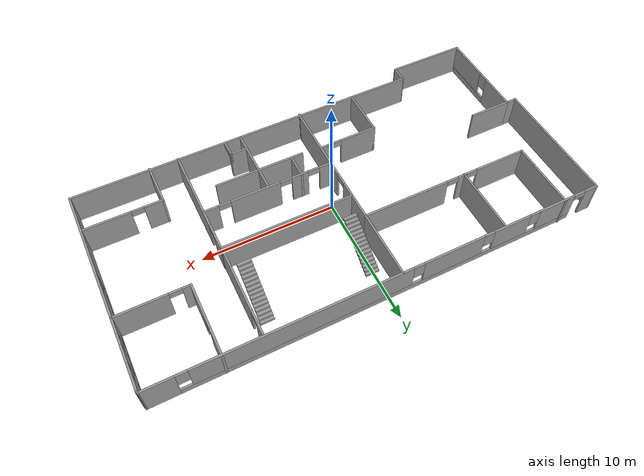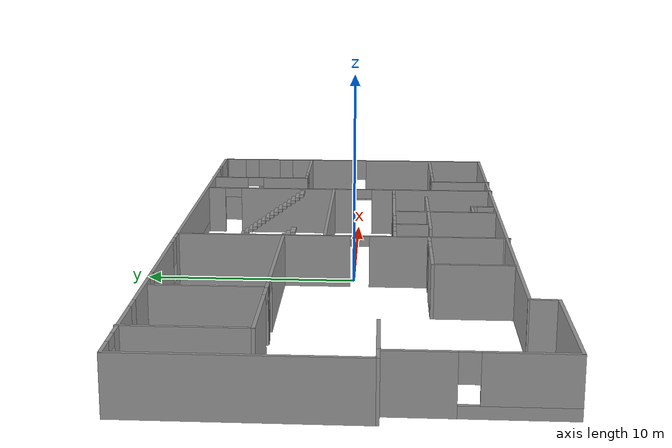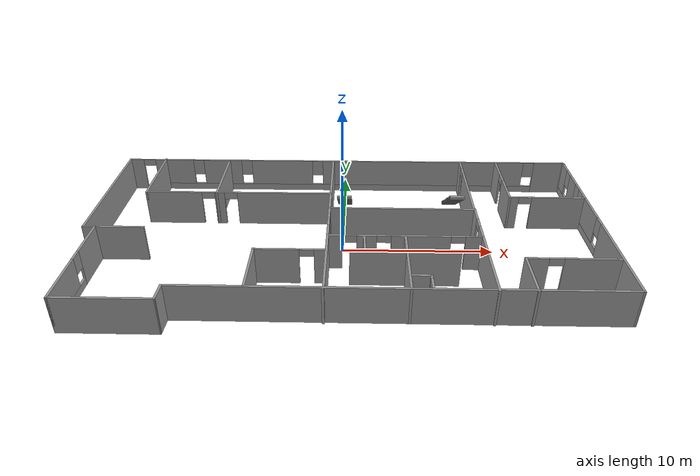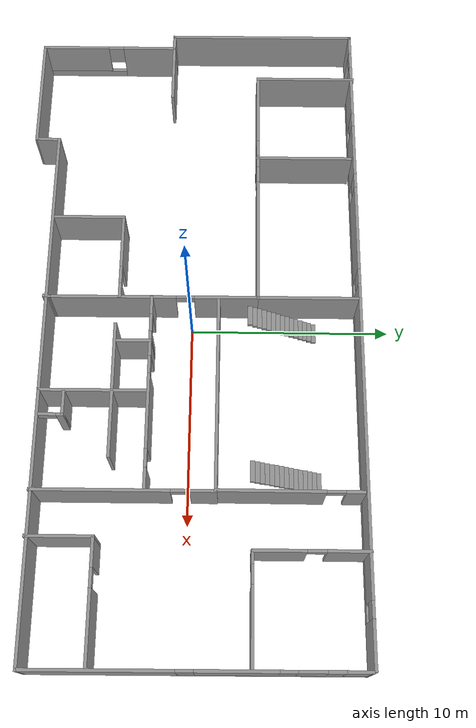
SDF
<?xml version='1.0'?>
<sdf version='1.7'>
  <model name='Dundler_mifflin'>
    <pose>0.058754 0.032766 0 0 -0 0</pose>
    <link name='Stairs_0'>
      <visual name='Stairs_0_Visual_0'>
        <pose>-0 6.1696 0.083333 0 -0 0</pose>
        <geometry>
          <box>
            <size>1 0.233333 0.166667</size>
          </box>
        </geometry>
        <material>
          <script>
            <uri>file://media/materials/scripts/gazebo.material</uri>
            <name>Gazebo/Grey</name>
          </script>
          <ambient>1 1 1 1</ambient>
        </material>
        <meta>
          <layer>0</layer>
        </meta>
      </visual>
      <collision name='Stairs_0_Collision_0'>
        <geometry>
          <box>
            <size>1 0.233333 0.166667</size>
          </box>
        </geometry>
        <pose>-0 6.1696 0.083333 0 -0 0</pose>
      </collision>
      <visual name='Stairs_0_Visual_1'>
        <pose>-0 5.93627 0.25 0 -0 0</pose>
        <geometry>
          <box>
            <size>1 0.233333 0.166667</size>
          </box>
        </geometry>
        <material>
          <script>
            <uri>file://media/materials/scripts/gazebo.material</uri>
            <name>Gazebo/Grey</name>
          </script>
          <ambient>1 1 1 1</ambient>
        </material>
        <meta>
          <layer>0</layer>
        </meta>
      </visual>
      <collision name='Stairs_0_Collision_1'>
        <geometry>
          <box>
            <size>1 0.233333 0.166667</size>
          </box>
        </geometry>
        <pose>-0 5.93627 0.25 0 -0 0</pose>
      </collision>
      <visual name='Stairs_0_Visual_2'>
        <pose>-0 5.70294 0.416667 0 -0 0</pose>
        <geometry>
          <box>
            <size>1 0.233333 0.166667</size>
          </box>
        </geometry>
        <material>
          <script>
            <uri>file://media/materials/scripts/gazebo.material</uri>
            <name>Gazebo/Grey</name>
          </script>
          <ambient>1 1 1 1</ambient>
        </material>
        <meta>
          <layer>0</layer>
        </meta>
      </visual>
      <collision name='Stairs_0_Collision_2'>
        <geometry>
          <box>
            <size>1 0.233333 0.166667</size>
          </box>
        </geometry>
        <pose>-0 5.70294 0.416667 0 -0 0</pose>
      </collision>
      <visual name='Stairs_0_Visual_3'>
        <pose>-0 5.4696 0.583333 0 -0 0</pose>
        <geometry>
          <box>
            <size>1 0.233333 0.166667</size>
          </box>
        </geometry>
        <material>
          <script>
            <uri>file://media/materials/scripts/gazebo.material</uri>
            <name>Gazebo/Grey</name>
          </script>
          <ambient>1 1 1 1</ambient>
        </material>
        <meta>
          <layer>0</layer>
        </meta>
      </visual>
      <collision name='Stairs_0_Collision_3'>
        <geometry>
          <box>
            <size>1 0.233333 0.166667</size>
          </box>
        </geometry>
        <pose>-0 5.4696 0.583333 0 -0 0</pose>
      </collision>
      <visual name='Stairs_0_Visual_4'>
        <pose>-0 5.23627 0.75 0 -0 0</pose>
        <geometry>
          <box>
            <size>1 0.233333 0.166667</size>
          </box>
        </geometry>
        <material>
          <script>
            <uri>file://media/materials/scripts/gazebo.material</uri>
            <name>Gazebo/Grey</name>
          </script>
          <ambient>1 1 1 1</ambient>
        </material>
        <meta>
          <layer>0</layer>
        </meta>
      </visual>
      <collision name='Stairs_0_Collision_4'>
        <geometry>
          <box>
            <size>1 0.233333 0.166667</size>
          </box>
        </geometry>
        <pose>-0 5.23627 0.75 0 -0 0</pose>
      </collision>
      <visual name='Stairs_0_Visual_5'>
        <pose>-0 5.00293 0.916667 0 -0 0</pose>
        <geometry>
          <box>
            <size>1 0.233333 0.166667</size>
          </box>
        </geometry>
        <material>
          <script>
            <uri>file://media/materials/scripts/gazebo.material</uri>
            <name>Gazebo/Grey</name>
          </script>
          <ambient>1 1 1 1</ambient>
        </material>
        <meta>
          <layer>0</layer>
        </meta>
      </visual>
      <collision name='Stairs_0_Collision_5'>
        <geometry>
          <box>
            <size>1 0.233333 0.166667</size>
          </box>
        </geometry>
        <pose>-0 5.00293 0.916667 0 -0 0</pose>
      </collision>
      <visual name='Stairs_0_Visual_6'>
        <pose>-0 4.7696 1.08333 0 -0 0</pose>
        <geometry>
          <box>
            <size>1 0.233333 0.166667</size>
          </box>
        </geometry>
        <material>
          <script>
            <uri>file://media/materials/scripts/gazebo.material</uri>
            <name>Gazebo/Grey</name>
          </script>
          <ambient>1 1 1 1</ambient>
        </material>
        <meta>
          <layer>0</layer>
        </meta>
      </visual>
      <collision name='Stairs_0_Collision_6'>
        <geometry>
          <box>
            <size>1 0.233333 0.166667</size>
          </box>
        </geometry>
        <pose>-0 4.7696 1.08333 0 -0 0</pose>
      </collision>
      <visual name='Stairs_0_Visual_7'>
        <pose>-0 4.53627 1.25 0 -0 0</pose>
        <geometry>
          <box>
            <size>1 0.233333 0.166667</size>
          </box>
        </geometry>
        <material>
          <script>
            <uri>file://media/materials/scripts/gazebo.material</uri>
            <name>Gazebo/Grey</name>
          </script>
          <ambient>1 1 1 1</ambient>
        </material>
        <meta>
          <layer>0</layer>
        </meta>
      </visual>
      <collision name='Stairs_0_Collision_7'>
        <geometry>
          <box>
            <size>1 0.233333 0.166667</size>
          </box>
        </geometry>
        <pose>-0 4.53627 1.25 0 -0 0</pose>
      </collision>
      <visual name='Stairs_0_Visual_8'>
        <pose>-0 4.30293 1.41667 0 -0 0</pose>
        <geometry>
          <box>
            <size>1 0.233333 0.166667</size>
          </box>
        </geometry>
        <material>
          <script>
            <uri>file://media/materials/scripts/gazebo.material</uri>
            <name>Gazebo/Grey</name>
          </script>
          <ambient>1 1 1 1</ambient>
        </material>
        <meta>
          <layer>0</layer>
        </meta>
      </visual>
      <collision name='Stairs_0_Collision_8'>
        <geometry>
          <box>
            <size>1 0.233333 0.166667</size>
          </box>
        </geometry>
        <pose>-0 4.30293 1.41667 0 -0 0</pose>
      </collision>
      <visual name='Stairs_0_Visual_9'>
        <pose>-0 4.0696 1.58333 0 -0 0</pose>
        <geometry>
          <box>
            <size>1 0.233333 0.166667</size>
          </box>
        </geometry>
        <material>
          <script>
            <uri>file://media/materials/scripts/gazebo.material</uri>
            <name>Gazebo/Grey</name>
          </script>
          <ambient>1 1 1 1</ambient>
        </material>
        <meta>
          <layer>0</layer>
        </meta>
      </visual>
      <collision name='Stairs_0_Collision_9'>
        <geometry>
          <box>
            <size>1 0.233333 0.166667</size>
          </box>
        </geometry>
        <pose>-0 4.0696 1.58333 0 -0 0</pose>
      </collision>
      <visual name='Stairs_0_Visual_10'>
        <pose>-0 3.83627 1.75 0 -0 0</pose>
        <geometry>
          <box>
            <size>1 0.233333 0.166667</size>
          </box>
        </geometry>
        <material>
          <script>
            <uri>file://media/materials/scripts/gazebo.material</uri>
            <name>Gazebo/Grey</name>
          </script>
          <ambient>1 1 1 1</ambient>
        </material>
        <meta>
          <layer>0</layer>
        </meta>
      </visual>
      <collision name='Stairs_0_Collision_10'>
        <geometry>
          <box>
            <size>1 0.233333 0.166667</size>
          </box>
        </geometry>
        <pose>-0 3.83627 1.75 0 -0 0</pose>
      </collision>
      <visual name='Stairs_0_Visual_11'>
        <pose>-0 3.60293 1.91667 0 -0 0</pose>
        <geometry>
          <box>
            <size>1 0.233333 0.166667</size>
          </box>
        </geometry>
        <material>
          <script>
            <uri>file://media/materials/scripts/gazebo.material</uri>
            <name>Gazebo/Grey</name>
          </script>
          <ambient>1 1 1 1</ambient>
        </material>
        <meta>
          <layer>0</layer>
        </meta>
      </visual>
      <collision name='Stairs_0_Collision_11'>
        <geometry>
          <box>
            <size>1 0.233333 0.166667</size>
          </box>
        </geometry>
        <pose>-0 3.60293 1.91667 0 -0 0</pose>
      </collision>
      <visual name='Stairs_0_Visual_12'>
        <pose>-0 3.3696 2.08333 0 -0 0</pose>
        <geometry>
          <box>
            <size>1 0.233333 0.166667</size>
          </box>
        </geometry>
        <material>
          <script>
            <uri>file://media/materials/scripts/gazebo.material</uri>
            <name>Gazebo/Grey</name>
          </script>
          <ambient>1 1 1 1</ambient>
        </material>
        <meta>
          <layer>0</layer>
        </meta>
      </visual>
      <collision name='Stairs_0_Collision_12'>
        <geometry>
          <box>
            <size>1 0.233333 0.166667</size>
          </box>
        </geometry>
        <pose>-0 3.3696 2.08333 0 -0 0</pose>
      </collision>
      <visual name='Stairs_0_Visual_13'>
        <pose>-0 3.13627 2.25 0 -0 0</pose>
        <geometry>
          <box>
            <size>1 0.233333 0.166667</size>
          </box>
        </geometry>
        <material>
          <script>
            <uri>file://media/materials/scripts/gazebo.material</uri>
            <name>Gazebo/Grey</name>
          </script>
          <ambient>1 1 1 1</ambient>
        </material>
        <meta>
          <layer>0</layer>
        </meta>
      </visual>
      <collision name='Stairs_0_Collision_13'>
        <geometry>
          <box>
            <size>1 0.233333 0.166667</size>
          </box>
        </geometry>
        <pose>-0 3.13627 2.25 0 -0 0</pose>
      </collision>
      <visual name='Stairs_0_Visual_14'>
        <pose>-0 2.90293 2.41667 0 -0 0</pose>
        <geometry>
          <box>
            <size>1 0.233333 0.166667</size>
          </box>
        </geometry>
        <material>
          <script>
            <uri>file://media/materials/scripts/gazebo.material</uri>
            <name>Gazebo/Grey</name>
          </script>
          <ambient>1 1 1 1</ambient>
        </material>
        <meta>
          <layer>0</layer>
        </meta>
      </visual>
      <collision name='Stairs_0_Collision_14'>
        <geometry>
          <box>
            <size>1 0.233333 0.166667</size>
          </box>
        </geometry>
        <pose>-0 2.90293 2.41667 0 -0 0</pose>
      </collision>
    </link>
    <link name='Stairs_1'>
      <visual name='Stairs_1_Visual_0'>
        <pose>7.80793 6.29097 0.083333 0 -0 0</pose>
        <geometry>
          <box>
            <size>1 0.233333 0.166667</size>
          </box>
        </geometry>
        <material>
          <script>
            <uri>file://media/materials/scripts/gazebo.material</uri>
            <name>Gazebo/Grey</name>
          </script>
          <ambient>1 1 1 1</ambient>
        </material>
        <meta>
          <layer>0</layer>
        </meta>
      </visual>
      <collision name='Stairs_1_Collision_0'>
        <geometry>
          <box>
            <size>1 0.233333 0.166667</size>
          </box>
        </geometry>
        <pose>7.80793 6.29097 0.083333 0 -0 0</pose>
      </collision>
      <visual name='Stairs_1_Visual_1'>
        <pose>7.80793 6.05764 0.25 0 -0 0</pose>
        <geometry>
          <box>
            <size>1 0.233333 0.166667</size>
          </box>
        </geometry>
        <material>
          <script>
            <uri>file://media/materials/scripts/gazebo.material</uri>
            <name>Gazebo/Grey</name>
          </script>
          <ambient>1 1 1 1</ambient>
        </material>
        <meta>
          <layer>0</layer>
        </meta>
      </visual>
      <collision name='Stairs_1_Collision_1'>
        <geometry>
          <box>
            <size>1 0.233333 0.166667</size>
          </box>
        </geometry>
        <pose>7.80793 6.05764 0.25 0 -0 0</pose>
      </collision>
      <visual name='Stairs_1_Visual_2'>
        <pose>7.80793 5.8243 0.416667 0 -0 0</pose>
        <geometry>
          <box>
            <size>1 0.233333 0.166667</size>
          </box>
        </geometry>
        <material>
          <script>
            <uri>file://media/materials/scripts/gazebo.material</uri>
            <name>Gazebo/Grey</name>
          </script>
          <ambient>1 1 1 1</ambient>
        </material>
        <meta>
          <layer>0</layer>
        </meta>
      </visual>
      <collision name='Stairs_1_Collision_2'>
        <geometry>
          <box>
            <size>1 0.233333 0.166667</size>
          </box>
        </geometry>
        <pose>7.80793 5.8243 0.416667 0 -0 0</pose>
      </collision>
      <visual name='Stairs_1_Visual_3'>
        <pose>7.80793 5.59097 0.583333 0 -0 0</pose>
        <geometry>
          <box>
            <size>1 0.233333 0.166667</size>
          </box>
        </geometry>
        <material>
          <script>
            <uri>file://media/materials/scripts/gazebo.material</uri>
            <name>Gazebo/Grey</name>
          </script>
          <ambient>1 1 1 1</ambient>
        </material>
        <meta>
          <layer>0</layer>
        </meta>
      </visual>
      <collision name='Stairs_1_Collision_3'>
        <geometry>
          <box>
            <size>1 0.233333 0.166667</size>
          </box>
        </geometry>
        <pose>7.80793 5.59097 0.583333 0 -0 0</pose>
      </collision>
      <visual name='Stairs_1_Visual_4'>
        <pose>7.80793 5.35764 0.75 0 -0 0</pose>
        <geometry>
          <box>
            <size>1 0.233333 0.166667</size>
          </box>
        </geometry>
        <material>
          <script>
            <uri>file://media/materials/scripts/gazebo.material</uri>
            <name>Gazebo/Grey</name>
          </script>
          <ambient>1 1 1 1</ambient>
        </material>
        <meta>
          <layer>0</layer>
        </meta>
      </visual>
      <collision name='Stairs_1_Collision_4'>
        <geometry>
          <box>
            <size>1 0.233333 0.166667</size>
          </box>
        </geometry>
        <pose>7.80793 5.35764 0.75 0 -0 0</pose>
      </collision>
      <visual name='Stairs_1_Visual_5'>
        <pose>7.80793 5.1243 0.916667 0 -0 0</pose>
        <geometry>
          <box>
            <size>1 0.233333 0.166667</size>
          </box>
        </geometry>
        <material>
          <script>
            <uri>file://media/materials/scripts/gazebo.material</uri>
            <name>Gazebo/Grey</name>
          </script>
          <ambient>1 1 1 1</ambient>
        </material>
        <meta>
          <layer>0</layer>
        </meta>
      </visual>
      <collision name='Stairs_1_Collision_5'>
        <geometry>
          <box>
            <size>1 0.233333 0.166667</size>
          </box>
        </geometry>
        <pose>7.80793 5.1243 0.916667 0 -0 0</pose>
      </collision>
      <visual name='Stairs_1_Visual_6'>
        <pose>7.80793 4.89097 1.08333 0 -0 0</pose>
        <geometry>
          <box>
            <size>1 0.233333 0.166667</size>
          </box>
        </geometry>
        <material>
          <script>
            <uri>file://media/materials/scripts/gazebo.material</uri>
            <name>Gazebo/Grey</name>
          </script>
          <ambient>1 1 1 1</ambient>
        </material>
        <meta>
          <layer>0</layer>
        </meta>
      </visual>
      <collision name='Stairs_1_Collision_6'>
        <geometry>
          <box>
            <size>1 0.233333 0.166667</size>
          </box>
        </geometry>
        <pose>7.80793 4.89097 1.08333 0 -0 0</pose>
      </collision>
      <visual name='Stairs_1_Visual_7'>
        <pose>7.80793 4.65763 1.25 0 -0 0</pose>
        <geometry>
          <box>
            <size>1 0.233333 0.166667</size>
          </box>
        </geometry>
        <material>
          <script>
            <uri>file://media/materials/scripts/gazebo.material</uri>
            <name>Gazebo/Grey</name>
          </script>
          <ambient>1 1 1 1</ambient>
        </material>
        <meta>
          <layer>0</layer>
        </meta>
      </visual>
      <collision name='Stairs_1_Collision_7'>
        <geometry>
          <box>
            <size>1 0.233333 0.166667</size>
          </box>
        </geometry>
        <pose>7.80793 4.65763 1.25 0 -0 0</pose>
      </collision>
      <visual name='Stairs_1_Visual_8'>
        <pose>7.80793 4.4243 1.41667 0 -0 0</pose>
        <geometry>
          <box>
            <size>1 0.233333 0.166667</size>
          </box>
        </geometry>
        <material>
          <script>
            <uri>file://media/materials/scripts/gazebo.material</uri>
            <name>Gazebo/Grey</name>
          </script>
          <ambient>1 1 1 1</ambient>
        </material>
        <meta>
          <layer>0</layer>
        </meta>
      </visual>
      <collision name='Stairs_1_Collision_8'>
        <geometry>
          <box>
            <size>1 0.233333 0.166667</size>
          </box>
        </geometry>
        <pose>7.80793 4.4243 1.41667 0 -0 0</pose>
      </collision>
      <visual name='Stairs_1_Visual_9'>
        <pose>7.80793 4.19097 1.58333 0 -0 0</pose>
        <geometry>
          <box>
            <size>1 0.233333 0.166667</size>
          </box>
        </geometry>
        <material>
          <script>
            <uri>file://media/materials/scripts/gazebo.material</uri>
            <name>Gazebo/Grey</name>
          </script>
          <ambient>1 1 1 1</ambient>
        </material>
        <meta>
          <layer>0</layer>
        </meta>
      </visual>
      <collision name='Stairs_1_Collision_9'>
        <geometry>
          <box>
            <size>1 0.233333 0.166667</size>
          </box>
        </geometry>
        <pose>7.80793 4.19097 1.58333 0 -0 0</pose>
      </collision>
      <visual name='Stairs_1_Visual_10'>
        <pose>7.80793 3.95763 1.75 0 -0 0</pose>
        <geometry>
          <box>
            <size>1 0.233333 0.166667</size>
          </box>
        </geometry>
        <material>
          <script>
            <uri>file://media/materials/scripts/gazebo.material</uri>
            <name>Gazebo/Grey</name>
          </script>
          <ambient>1 1 1 1</ambient>
        </material>
        <meta>
          <layer>0</layer>
        </meta>
      </visual>
      <collision name='Stairs_1_Collision_10'>
        <geometry>
          <box>
            <size>1 0.233333 0.166667</size>
          </box>
        </geometry>
        <pose>7.80793 3.95763 1.75 0 -0 0</pose>
      </collision>
      <visual name='Stairs_1_Visual_11'>
        <pose>7.80793 3.7243 1.91667 0 -0 0</pose>
        <geometry>
          <box>
            <size>1 0.233333 0.166667</size>
          </box>
        </geometry>
        <material>
          <script>
            <uri>file://media/materials/scripts/gazebo.material</uri>
            <name>Gazebo/Grey</name>
          </script>
          <ambient>1 1 1 1</ambient>
        </material>
        <meta>
          <layer>0</layer>
        </meta>
      </visual>
      <collision name='Stairs_1_Collision_11'>
        <geometry>
          <box>
            <size>1 0.233333 0.166667</size>
          </box>
        </geometry>
        <pose>7.80793 3.7243 1.91667 0 -0 0</pose>
      </collision>
      <visual name='Stairs_1_Visual_12'>
        <pose>7.80793 3.49097 2.08333 0 -0 0</pose>
        <geometry>
          <box>
            <size>1 0.233333 0.166667</size>
          </box>
        </geometry>
        <material>
          <script>
            <uri>file://media/materials/scripts/gazebo.material</uri>
            <name>Gazebo/Grey</name>
          </script>
          <ambient>1 1 1 1</ambient>
        </material>
        <meta>
          <layer>0</layer>
        </meta>
      </visual>
      <collision name='Stairs_1_Collision_12'>
        <geometry>
          <box>
            <size>1 0.233333 0.166667</size>
          </box>
        </geometry>
        <pose>7.80793 3.49097 2.08333 0 -0 0</pose>
      </collision>
      <visual name='Stairs_1_Visual_13'>
        <pose>7.80793 3.25764 2.25 0 -0 0</pose>
        <geometry>
          <box>
            <size>1 0.233333 0.166667</size>
          </box>
        </geometry>
        <material>
          <script>
            <uri>file://media/materials/scripts/gazebo.material</uri>
            <name>Gazebo/Grey</name>
          </script>
          <ambient>1 1 1 1</ambient>
        </material>
        <meta>
          <layer>0</layer>
        </meta>
      </visual>
      <collision name='Stairs_1_Collision_13'>
        <geometry>
          <box>
            <size>1 0.233333 0.166667</size>
          </box>
        </geometry>
        <pose>7.80793 3.25764 2.25 0 -0 0</pose>
      </collision>
      <visual name='Stairs_1_Visual_14'>
        <pose>7.80793 3.0243 2.41667 0 -0 0</pose>
        <geometry>
          <box>
            <size>1 0.233333 0.166667</size>
          </box>
        </geometry>
        <material>
          <script>
            <uri>file://media/materials/scripts/gazebo.material</uri>
            <name>Gazebo/Grey</name>
          </script>
          <ambient>1 1 1 1</ambient>
        </material>
        <meta>
          <layer>0</layer>
        </meta>
      </visual>
      <collision name='Stairs_1_Collision_14'>
        <geometry>
          <box>
            <size>1 0.233333 0.166667</size>
          </box>
        </geometry>
        <pose>7.80793 3.0243 2.41667 0 -0 0</pose>
      </collision>
    </link>
    <link name='Wall_0'>
      <collision name='Wall_0_Collision'>
        <geometry>
          <box>
            <size>9.73708 0.15 2.5</size>
          </box>
        </geometry>
        <pose>0 0 1.25 0 -0 0</pose>
      </collision>
      <visual name='Wall_0_Visual'>
        <pose>0 0 1.25 0 -0 0</pose>
        <geometry>
          <box>
            <size>9.73708 0.15 2.5</size>
          </box>
        </geometry>
        <material>
          <script>
            <uri>file://media/materials/scripts/gazebo.material</uri>
            <name>Gazebo/Grey</name>
          </script>
          <ambient>1 1 1 1</ambient>
        </material>
        <meta>
          <layer>0</layer>
        </meta>
      </visual>
      <pose>-16.6238 3.54458 0 0 -0 -1.56939</pose>
    </link>
    <link name='Wall_1'>
      <collision name='Wall_1_Collision'>
        <geometry>
          <box>
            <size>0.906952 0.15 2.5</size>
          </box>
        </geometry>
        <pose>0 0 1.25 0 -0 0</pose>
      </collision>
      <visual name='Wall_1_Visual'>
        <pose>0 0 1.25 0 -0 0</pose>
        <geometry>
          <box>
            <size>0.906952 0.15 2.5</size>
          </box>
        </geometry>
        <material>
          <script>
            <uri>file://media/materials/scripts/gazebo.material</uri>
            <name>Gazebo/Grey</name>
          </script>
          <ambient>1 1 1 1</ambient>
        </material>
        <meta>
          <layer>0</layer>
        </meta>
      </visual>
      <pose>-16.2386 -1.29532 0 0 -0 0</pose>
    </link>
    <link name='Wall_10'>
      <collision name='Wall_10_Collision'>
        <geometry>
          <box>
            <size>5.25 0.15 2.5</size>
          </box>
        </geometry>
        <pose>0 0 1.25 0 -0 0</pose>
      </collision>
      <visual name='Wall_10_Visual'>
        <pose>0 0 1.25 0 -0 0</pose>
        <geometry>
          <box>
            <size>5.25 0.15 2.5</size>
          </box>
        </geometry>
        <material>
          <script>
            <uri>file://media/materials/scripts/gazebo.material</uri>
            <name>Gazebo/Grey</name>
          </script>
          <ambient>1 1 1 1</ambient>
        </material>
        <meta>
          <layer>0</layer>
        </meta>
      </visual>
      <pose>-13.8957 5.8475 0 0 -0 -1.5708</pose>
    </link>
    <link name='Wall_11'>
      <pose>-7.43051 3.2975 0 0 -0 0</pose>
      <visual name='Wall_11_Visual_0'>
        <pose>-4.55815 0 1.25 0 -0 0</pose>
        <geometry>
          <box>
            <size>3.96416 0.15 2.5</size>
          </box>
        </geometry>
        <material>
          <script>
            <uri>file://media/materials/scripts/gazebo.material</uri>
            <name>Gazebo/Grey</name>
          </script>
          <ambient>1 1 1 1</ambient>
        </material>
        <meta>
          <layer>0</layer>
        </meta>
      </visual>
      <collision name='Wall_11_Collision_0'>
        <geometry>
          <box>
            <size>3.96416 0.15 2.5</size>
          </box>
        </geometry>
        <pose>-4.55815 0 1.25 0 -0 0</pose>
      </collision>
      <visual name='Wall_11_Visual_1'>
        <pose>-1.33225 0 1.25 0 -0 0</pose>
        <geometry>
          <box>
            <size>0.687646 0.15 2.5</size>
          </box>
        </geometry>
        <material>
          <script>
            <uri>file://media/materials/scripts/gazebo.material</uri>
            <name>Gazebo/Grey</name>
          </script>
          <ambient>1 1 1 1</ambient>
        </material>
        <meta>
          <layer>0</layer>
        </meta>
      </visual>
      <collision name='Wall_11_Collision_1'>
        <geometry>
          <box>
            <size>0.687646 0.15 2.5</size>
          </box>
        </geometry>
        <pose>-1.33225 0 1.25 0 -0 0</pose>
      </collision>
      <visual name='Wall_11_Visual_2'>
        <pose>3.2259 0 1.25 0 -0 0</pose>
        <geometry>
          <box>
            <size>6.62865 0.15 2.5</size>
          </box>
        </geometry>
        <material>
          <script>
            <uri>file://media/materials/scripts/gazebo.material</uri>
            <name>Gazebo/Grey</name>
          </script>
          <ambient>1 1 1 1</ambient>
        </material>
        <meta>
          <layer>0</layer>
        </meta>
      </visual>
      <collision name='Wall_11_Collision_2'>
        <geometry>
          <box>
            <size>6.62865 0.15 2.5</size>
          </box>
        </geometry>
        <pose>3.2259 0 1.25 0 -0 0</pose>
      </collision>
      <visual name='Wall_11_Visual_3'>
        <pose>-2.12607 0 2.25 0 -0 0</pose>
        <geometry>
          <box>
            <size>0.9 0.15 0.5</size>
          </box>
        </geometry>
        <material>
          <script>
            <uri>file://media/materials/scripts/gazebo.material</uri>
            <name>Gazebo/Grey</name>
          </script>
          <ambient>1 1 1 1</ambient>
        </material>
        <meta>
          <layer>0</layer>
        </meta>
      </visual>
      <collision name='Wall_11_Collision_3'>
        <geometry>
          <box>
            <size>0.9 0.15 0.5</size>
          </box>
        </geometry>
        <pose>-2.12607 0 2.25 0 -0 0</pose>
      </collision>
      <visual name='Wall_11_Visual_4'>
        <pose>-0.538423 0 2.25 0 -0 0</pose>
        <geometry>
          <box>
            <size>0.9 0.15 0.5</size>
          </box>
        </geometry>
        <material>
          <script>
            <uri>file://media/materials/scripts/gazebo.material</uri>
            <name>Gazebo/Grey</name>
          </script>
          <ambient>1 1 1 1</ambient>
        </material>
        <meta>
          <layer>0</layer>
        </meta>
      </visual>
      <collision name='Wall_11_Collision_4'>
        <geometry>
          <box>
            <size>0.9 0.15 0.5</size>
          </box>
        </geometry>
        <pose>-0.538423 0 2.25 0 -0 0</pose>
      </collision>
    </link>
    <link name='Wall_12'>
      <pose>-0.955224 -1.88756 0 0 -0 -1.56886</pose>
      <visual name='Wall_12_Visual_0'>
        <pose>-3.63589 0 1.25 0 -0 0</pose>
        <geometry>
          <box>
            <size>3.24835 0.15 2.5</size>
          </box>
        </geometry>
        <material>
          <script>
            <uri>file://media/materials/scripts/gazebo.material</uri>
            <name>Gazebo/Grey</name>
          </script>
          <ambient>1 1 1 1</ambient>
        </material>
        <meta>
          <layer>0</layer>
        </meta>
      </visual>
      <collision name='Wall_12_Collision_0'>
        <geometry>
          <box>
            <size>3.24835 0.15 2.5</size>
          </box>
        </geometry>
        <pose>-3.63589 0 1.25 0 -0 0</pose>
      </collision>
      <visual name='Wall_12_Visual_1'>
        <pose>2.07418 0 1.25 0 -0 0</pose>
        <geometry>
          <box>
            <size>6.37178 0.15 2.5</size>
          </box>
        </geometry>
        <material>
          <script>
            <uri>file://media/materials/scripts/gazebo.material</uri>
            <name>Gazebo/Grey</name>
          </script>
          <ambient>1 1 1 1</ambient>
        </material>
        <meta>
          <layer>0</layer>
        </meta>
      </visual>
      <collision name='Wall_12_Collision_1'>
        <geometry>
          <box>
            <size>6.37178 0.15 2.5</size>
          </box>
        </geometry>
        <pose>2.07418 0 1.25 0 -0 0</pose>
      </collision>
      <visual name='Wall_12_Visual_2'>
        <pose>-1.56171 0 2.25 0 -0 0</pose>
        <geometry>
          <box>
            <size>0.9 0.15 0.5</size>
          </box>
        </geometry>
        <material>
          <script>
            <uri>file://media/materials/scripts/gazebo.material</uri>
            <name>Gazebo/Grey</name>
          </script>
          <ambient>1 1 1 1</ambient>
        </material>
        <meta>
          <layer>0</layer>
        </meta>
      </visual>
      <collision name='Wall_12_Collision_2'>
        <geometry>
          <box>
            <size>0.9 0.15 0.5</size>
          </box>
        </geometry>
        <pose>-1.56171 0 2.25 0 -0 0</pose>
      </collision>
    </link>
    <link name='Wall_14'>
      <collision name='Wall_14_Collision'>
        <geometry>
          <box>
            <size>0.402154 0.15 2.5</size>
          </box>
        </geometry>
        <pose>0 0 1.25 0 -0 0</pose>
      </collision>
      <visual name='Wall_14_Visual'>
        <pose>0 0 1.25 0 -0 0</pose>
        <geometry>
          <box>
            <size>0.402154 0.15 2.5</size>
          </box>
        </geometry>
        <material>
          <script>
            <uri>file://media/materials/scripts/gazebo.material</uri>
            <name>Gazebo/Grey</name>
          </script>
          <ambient>1 1 1 1</ambient>
        </material>
        <meta>
          <layer>0</layer>
        </meta>
      </visual>
      <pose>-0.960057 -7.19781 0 0 -0 1.45242</pose>
    </link>
    <link name='Wall_16'>
      <collision name='Wall_16_Collision'>
        <geometry>
          <box>
            <size>9.72356 0.15 2.5</size>
          </box>
        </geometry>
        <pose>0 0 1.25 0 -0 0</pose>
      </collision>
      <visual name='Wall_16_Visual'>
        <pose>0 0 1.25 0 -0 0</pose>
        <geometry>
          <box>
            <size>9.72356 0.15 2.5</size>
          </box>
        </geometry>
        <material>
          <script>
            <uri>file://media/materials/scripts/gazebo.material</uri>
            <name>Gazebo/Grey</name>
          </script>
          <ambient>1 1 1 1</ambient>
        </material>
        <meta>
          <layer>0</layer>
        </meta>
      </visual>
      <pose>3.91536 1.33297 0 0 -0 -0.001938</pose>
    </link>
    <link name='Wall_17'>
      <pose>8.71536 4.75797 0 0 -0 1.56694</pose>
      <visual name='Wall_17_Visual_0'>
        <pose>-0.909005 0 1.25 0 -0 0</pose>
        <geometry>
          <box>
            <size>5.20056 0.15 2.5</size>
          </box>
        </geometry>
        <material>
          <script>
            <uri>file://media/materials/scripts/gazebo.material</uri>
            <name>Gazebo/Grey</name>
          </script>
          <ambient>1 1 1 1</ambient>
        </material>
        <meta>
          <layer>0</layer>
        </meta>
      </visual>
      <collision name='Wall_17_Collision_0'>
        <geometry>
          <box>
            <size>5.20056 0.15 2.5</size>
          </box>
        </geometry>
        <pose>-0.909005 0 1.25 0 -0 0</pose>
      </collision>
      <visual name='Wall_17_Visual_1'>
        <pose>3.05028 0 1.25 0 -0 0</pose>
        <geometry>
          <box>
            <size>0.91801 0.15 2.5</size>
          </box>
        </geometry>
        <material>
          <script>
            <uri>file://media/materials/scripts/gazebo.material</uri>
            <name>Gazebo/Grey</name>
          </script>
          <ambient>1 1 1 1</ambient>
        </material>
        <meta>
          <layer>0</layer>
        </meta>
      </visual>
      <collision name='Wall_17_Collision_1'>
        <geometry>
          <box>
            <size>0.91801 0.15 2.5</size>
          </box>
        </geometry>
        <pose>3.05028 0 1.25 0 -0 0</pose>
      </collision>
      <visual name='Wall_17_Visual_2'>
        <pose>2.14127 0 2.25 0 -0 0</pose>
        <geometry>
          <box>
            <size>0.9 0.15 0.5</size>
          </box>
        </geometry>
        <material>
          <script>
            <uri>file://media/materials/scripts/gazebo.material</uri>
            <name>Gazebo/Grey</name>
          </script>
          <ambient>1 1 1 1</ambient>
        </material>
        <meta>
          <layer>0</layer>
        </meta>
      </visual>
      <collision name='Wall_17_Collision_2'>
        <geometry>
          <box>
            <size>0.9 0.15 0.5</size>
          </box>
        </geometry>
        <pose>2.14127 0 2.25 0 -0 0</pose>
      </collision>
    </link>
    <link name='Wall_19'>
      <pose>8.74259 -2.97631 0 0 -0 -1.5708</pose>
      <visual name='Wall_19_Visual_0'>
        <pose>-3.73996 0 1.25 0 -0 0</pose>
        <geometry>
          <box>
            <size>1.27008 0.15 2.5</size>
          </box>
        </geometry>
        <material>
          <script>
            <uri>file://media/materials/scripts/gazebo.material</uri>
            <name>Gazebo/Grey</name>
          </script>
          <ambient>1 1 1 1</ambient>
        </material>
        <meta>
          <layer>0</layer>
        </meta>
      </visual>
      <collision name='Wall_19_Collision_0'>
        <geometry>
          <box>
            <size>1.27008 0.15 2.5</size>
          </box>
        </geometry>
        <pose>-3.73996 0 1.25 0 -0 0</pose>
      </collision>
      <visual name='Wall_19_Visual_1'>
        <pose>1.08504 0 1.25 0 -0 0</pose>
        <geometry>
          <box>
            <size>6.57992 0.15 2.5</size>
          </box>
        </geometry>
        <material>
          <script>
            <uri>file://media/materials/scripts/gazebo.material</uri>
            <name>Gazebo/Grey</name>
          </script>
          <ambient>1 1 1 1</ambient>
        </material>
        <meta>
          <layer>0</layer>
        </meta>
      </visual>
      <collision name='Wall_19_Collision_1'>
        <geometry>
          <box>
            <size>6.57992 0.15 2.5</size>
          </box>
        </geometry>
        <pose>1.08504 0 1.25 0 -0 0</pose>
      </collision>
      <visual name='Wall_19_Visual_2'>
        <pose>-2.65492 0 2.25 0 -0 0</pose>
        <geometry>
          <box>
            <size>0.9 0.15 0.5</size>
          </box>
        </geometry>
        <material>
          <script>
            <uri>file://media/materials/scripts/gazebo.material</uri>
            <name>Gazebo/Grey</name>
          </script>
          <ambient>1 1 1 1</ambient>
        </material>
        <meta>
          <layer>0</layer>
        </meta>
      </visual>
      <collision name='Wall_19_Collision_2'>
        <geometry>
          <box>
            <size>0.9 0.15 0.5</size>
          </box>
        </geometry>
        <pose>-2.65492 0 2.25 0 -0 0</pose>
      </collision>
    </link>
    <link name='Wall_2'>
      <pose>-15.8601 -4.84532 0 0 -0 -1.5708</pose>
      <visual name='Wall_2_Visual_0'>
        <pose>-2.1925 0 1.25 0 -0 0</pose>
        <geometry>
          <box>
            <size>2.865 0.15 2.5</size>
          </box>
        </geometry>
        <material>
          <script>
            <uri>file://media/materials/scripts/gazebo.material</uri>
            <name>Gazebo/Grey</name>
          </script>
          <ambient>1 1 1 1</ambient>
        </material>
        <meta>
          <layer>0</layer>
        </meta>
      </visual>
      <collision name='Wall_2_Collision_0'>
        <geometry>
          <box>
            <size>2.865 0.15 2.5</size>
          </box>
        </geometry>
        <pose>-2.1925 0 1.25 0 -0 0</pose>
      </collision>
      <visual name='Wall_2_Visual_1'>
        <pose>1.4325 0 0.25 0 -0 0</pose>
        <geometry>
          <box>
            <size>4.385 0.15 0.5</size>
          </box>
        </geometry>
        <material>
          <script>
            <uri>file://media/materials/scripts/gazebo.material</uri>
            <name>Gazebo/Grey</name>
          </script>
          <ambient>1 1 1 1</ambient>
        </material>
        <meta>
          <layer>0</layer>
        </meta>
      </visual>
      <collision name='Wall_2_Collision_1'>
        <geometry>
          <box>
            <size>4.385 0.15 0.5</size>
          </box>
        </geometry>
        <pose>1.4325 0 0.25 0 -0 0</pose>
      </collision>
      <visual name='Wall_2_Visual_2'>
        <pose>1.8325 0 1.5 0 -0 0</pose>
        <geometry>
          <box>
            <size>3.585 0.15 2</size>
          </box>
        </geometry>
        <material>
          <script>
            <uri>file://media/materials/scripts/gazebo.material</uri>
            <name>Gazebo/Grey</name>
          </script>
          <ambient>1 1 1 1</ambient>
        </material>
        <meta>
          <layer>0</layer>
        </meta>
      </visual>
      <collision name='Wall_2_Collision_2'>
        <geometry>
          <box>
            <size>3.585 0.15 2</size>
          </box>
        </geometry>
        <pose>1.8325 0 1.5 0 -0 0</pose>
      </collision>
      <visual name='Wall_2_Visual_3'>
        <pose>-0.359998 0 1.9 0 -0 0</pose>
        <geometry>
          <box>
            <size>0.8 0.15 1.2</size>
          </box>
        </geometry>
        <material>
          <script>
            <uri>file://media/materials/scripts/gazebo.material</uri>
            <name>Gazebo/Grey</name>
          </script>
          <ambient>1 1 1 1</ambient>
        </material>
        <meta>
          <layer>0</layer>
        </meta>
      </visual>
      <collision name='Wall_2_Collision_3'>
        <geometry>
          <box>
            <size>0.8 0.15 1.2</size>
          </box>
        </geometry>
        <pose>-0.359998 0 1.9 0 -0 0</pose>
      </collision>
    </link>
    <link name='Wall_21'>
      <pose>3.86393 -1.97588 0 0 -0 0</pose>
      <visual name='Wall_21_Visual_0'>
        <pose>-4.38876 0 1.25 0 -0 0</pose>
        <geometry>
          <box>
            <size>0.972488 0.15 2.5</size>
          </box>
        </geometry>
        <material>
          <script>
            <uri>file://media/materials/scripts/gazebo.material</uri>
            <name>Gazebo/Grey</name>
          </script>
          <ambient>1 1 1 1</ambient>
        </material>
        <meta>
          <layer>0</layer>
        </meta>
      </visual>
      <collision name='Wall_21_Collision_0'>
        <geometry>
          <box>
            <size>0.972488 0.15 2.5</size>
          </box>
        </geometry>
        <pose>-4.38876 0 1.25 0 -0 0</pose>
      </collision>
      <visual name='Wall_21_Visual_1'>
        <pose>-2.36833 0 1.25 0 -0 0</pose>
        <geometry>
          <box>
            <size>1.26836 0.15 2.5</size>
          </box>
        </geometry>
        <material>
          <script>
            <uri>file://media/materials/scripts/gazebo.material</uri>
            <name>Gazebo/Grey</name>
          </script>
          <ambient>1 1 1 1</ambient>
        </material>
        <meta>
          <layer>0</layer>
        </meta>
      </visual>
      <collision name='Wall_21_Collision_1'>
        <geometry>
          <box>
            <size>1.26836 0.15 2.5</size>
          </box>
        </geometry>
        <pose>-2.36833 0 1.25 0 -0 0</pose>
      </collision>
      <visual name='Wall_21_Visual_2'>
        <pose>1.02891 0 1.25 0 -0 0</pose>
        <geometry>
          <box>
            <size>3.72612 0.15 2.5</size>
          </box>
        </geometry>
        <material>
          <script>
            <uri>file://media/materials/scripts/gazebo.material</uri>
            <name>Gazebo/Grey</name>
          </script>
          <ambient>1 1 1 1</ambient>
        </material>
        <meta>
          <layer>0</layer>
        </meta>
      </visual>
      <collision name='Wall_21_Collision_2'>
        <geometry>
          <box>
            <size>3.72612 0.15 2.5</size>
          </box>
        </geometry>
        <pose>1.02891 0 1.25 0 -0 0</pose>
      </collision>
      <visual name='Wall_21_Visual_3'>
        <pose>4.33349 0 1.25 0 -0 0</pose>
        <geometry>
          <box>
            <size>1.08303 0.15 2.5</size>
          </box>
        </geometry>
        <material>
          <script>
            <uri>file://media/materials/scripts/gazebo.material</uri>
            <name>Gazebo/Grey</name>
          </script>
          <ambient>1 1 1 1</ambient>
        </material>
        <meta>
          <layer>0</layer>
        </meta>
      </visual>
      <collision name='Wall_21_Collision_3'>
        <geometry>
          <box>
            <size>1.08303 0.15 2.5</size>
          </box>
        </geometry>
        <pose>4.33349 0 1.25 0 -0 0</pose>
      </collision>
      <visual name='Wall_21_Visual_4'>
        <pose>-3.45251 0 2.25 0 -0 0</pose>
        <geometry>
          <box>
            <size>0.9 0.15 0.5</size>
          </box>
        </geometry>
        <material>
          <script>
            <uri>file://media/materials/scripts/gazebo.material</uri>
            <name>Gazebo/Grey</name>
          </script>
          <ambient>1 1 1 1</ambient>
        </material>
        <meta>
          <layer>0</layer>
        </meta>
      </visual>
      <collision name='Wall_21_Collision_4'>
        <geometry>
          <box>
            <size>0.9 0.15 0.5</size>
          </box>
        </geometry>
        <pose>-3.45251 0 2.25 0 -0 0</pose>
      </collision>
      <visual name='Wall_21_Visual_5'>
        <pose>-1.28415 0 2.25 0 -0 0</pose>
        <geometry>
          <box>
            <size>0.9 0.15 0.5</size>
          </box>
        </geometry>
        <material>
          <script>
            <uri>file://media/materials/scripts/gazebo.material</uri>
            <name>Gazebo/Grey</name>
          </script>
          <ambient>1 1 1 1</ambient>
        </material>
        <meta>
          <layer>0</layer>
        </meta>
      </visual>
      <collision name='Wall_21_Collision_5'>
        <geometry>
          <box>
            <size>0.9 0.15 0.5</size>
          </box>
        </geometry>
        <pose>-1.28415 0 2.25 0 -0 0</pose>
      </collision>
      <visual name='Wall_21_Visual_6'>
        <pose>3.34197 0 2.25 0 -0 0</pose>
        <geometry>
          <box>
            <size>0.9 0.15 0.5</size>
          </box>
        </geometry>
        <material>
          <script>
            <uri>file://media/materials/scripts/gazebo.material</uri>
            <name>Gazebo/Grey</name>
          </script>
          <ambient>1 1 1 1</ambient>
        </material>
        <meta>
          <layer>0</layer>
        </meta>
      </visual>
      <collision name='Wall_21_Collision_6'>
        <geometry>
          <box>
            <size>0.9 0.15 0.5</size>
          </box>
        </geometry>
        <pose>3.34197 0 2.25 0 -0 0</pose>
      </collision>
    </link>
    <link name='Wall_23'>
      <collision name='Wall_23_Collision'>
        <geometry>
          <box>
            <size>5.25 0.15 2.5</size>
          </box>
        </geometry>
        <pose>0 0 1.25 0 -0 0</pose>
      </collision>
      <visual name='Wall_23_Visual'>
        <pose>0 0 1.25 0 -0 0</pose>
        <geometry>
          <box>
            <size>5.25 0.15 2.5</size>
          </box>
        </geometry>
        <material>
          <script>
            <uri>file://media/materials/scripts/gazebo.material</uri>
            <name>Gazebo/Grey</name>
          </script>
          <ambient>1 1 1 1</ambient>
        </material>
        <meta>
          <layer>0</layer>
        </meta>
      </visual>
      <pose>3.92136 -4.66467 0 0 -0 -1.5708</pose>
    </link>
    <link name='Wall_25'>
      <collision name='Wall_25_Collision'>
        <geometry>
          <box>
            <size>6.75 0.15 2.5</size>
          </box>
        </geometry>
        <pose>0 0 1.25 0 -0 0</pose>
      </collision>
      <visual name='Wall_25_Visual'>
        <pose>0 0 1.25 0 -0 0</pose>
        <geometry>
          <box>
            <size>6.75 0.15 2.5</size>
          </box>
        </geometry>
        <material>
          <script>
            <uri>file://media/materials/scripts/gazebo.material</uri>
            <name>Gazebo/Grey</name>
          </script>
          <ambient>1 1 1 1</ambient>
        </material>
        <meta>
          <layer>0</layer>
        </meta>
      </visual>
      <pose>3.82116 -3.71068 0 0 -0 0</pose>
    </link>
    <link name='Wall_27'>
      <pose>11.4275 5.71132 0 0 -0 -1.5708</pose>
      <visual name='Wall_27_Visual_0'>
        <pose>-1.71906 0 1.25 0 -0 0</pose>
        <geometry>
          <box>
            <size>2.06188 0.15 2.5</size>
          </box>
        </geometry>
        <material>
          <script>
            <uri>file://media/materials/scripts/gazebo.material</uri>
            <name>Gazebo/Grey</name>
          </script>
          <ambient>1 1 1 1</ambient>
        </material>
        <meta>
          <layer>0</layer>
        </meta>
      </visual>
      <collision name='Wall_27_Collision_0'>
        <geometry>
          <box>
            <size>2.06188 0.15 2.5</size>
          </box>
        </geometry>
        <pose>-1.71906 0 1.25 0 -0 0</pose>
      </collision>
      <visual name='Wall_27_Visual_1'>
        <pose>1.48094 0 1.25 0 -0 0</pose>
        <geometry>
          <box>
            <size>2.53812 0.15 2.5</size>
          </box>
        </geometry>
        <material>
          <script>
            <uri>file://media/materials/scripts/gazebo.material</uri>
            <name>Gazebo/Grey</name>
          </script>
          <ambient>1 1 1 1</ambient>
        </material>
        <meta>
          <layer>0</layer>
        </meta>
      </visual>
      <collision name='Wall_27_Collision_1'>
        <geometry>
          <box>
            <size>2.53812 0.15 2.5</size>
          </box>
        </geometry>
        <pose>1.48094 0 1.25 0 -0 0</pose>
      </collision>
      <visual name='Wall_27_Visual_2'>
        <pose>-0.238121 0 2.25 0 -0 0</pose>
        <geometry>
          <box>
            <size>0.9 0.15 0.5</size>
          </box>
        </geometry>
        <material>
          <script>
            <uri>file://media/materials/scripts/gazebo.material</uri>
            <name>Gazebo/Grey</name>
          </script>
          <ambient>1 1 1 1</ambient>
        </material>
        <meta>
          <layer>0</layer>
        </meta>
      </visual>
      <collision name='Wall_27_Collision_2'>
        <geometry>
          <box>
            <size>0.9 0.15 0.5</size>
          </box>
        </geometry>
        <pose>-0.238121 0 2.25 0 -0 0</pose>
      </collision>
    </link>
    <link name='Wall_28'>
      <pose>13.9775 3.03632 0 0 -0 0</pose>
      <visual name='Wall_28_Visual_0'>
        <pose>-2.28737 0 1.25 0 -0 0</pose>
        <geometry>
          <box>
            <size>0.675255 0.15 2.5</size>
          </box>
        </geometry>
        <material>
          <script>
            <uri>file://media/materials/scripts/gazebo.material</uri>
            <name>Gazebo/Grey</name>
          </script>
          <ambient>1 1 1 1</ambient>
        </material>
        <meta>
          <layer>0</layer>
        </meta>
      </visual>
      <collision name='Wall_28_Collision_0'>
        <geometry>
          <box>
            <size>0.675255 0.15 2.5</size>
          </box>
        </geometry>
        <pose>-2.28737 0 1.25 0 -0 0</pose>
      </collision>
      <visual name='Wall_28_Visual_1'>
        <pose>0.787627 0 1.25 0 -0 0</pose>
        <geometry>
          <box>
            <size>3.67475 0.15 2.5</size>
          </box>
        </geometry>
        <material>
          <script>
            <uri>file://media/materials/scripts/gazebo.material</uri>
            <name>Gazebo/Grey</name>
          </script>
          <ambient>1 1 1 1</ambient>
        </material>
        <meta>
          <layer>0</layer>
        </meta>
      </visual>
      <collision name='Wall_28_Collision_1'>
        <geometry>
          <box>
            <size>3.67475 0.15 2.5</size>
          </box>
        </geometry>
        <pose>0.787627 0 1.25 0 -0 0</pose>
      </collision>
      <visual name='Wall_28_Visual_2'>
        <pose>-1.49975 0 2.25 0 -0 0</pose>
        <geometry>
          <box>
            <size>0.9 0.15 0.5</size>
          </box>
        </geometry>
        <material>
          <script>
            <uri>file://media/materials/scripts/gazebo.material</uri>
            <name>Gazebo/Grey</name>
          </script>
          <ambient>1 1 1 1</ambient>
        </material>
        <meta>
          <layer>0</layer>
        </meta>
      </visual>
      <collision name='Wall_28_Collision_2'>
        <geometry>
          <box>
            <size>0.9 0.15 0.5</size>
          </box>
        </geometry>
        <pose>-1.49975 0 2.25 0 -0 0</pose>
      </collision>
    </link>
    <link name='Wall_3'>
      <collision name='Wall_3_Collision'>
        <geometry>
          <box>
            <size>6 0.15 2.5</size>
          </box>
        </geometry>
        <pose>0 0 1.25 0 -0 0</pose>
      </collision>
      <visual name='Wall_3_Visual'>
        <pose>0 0 1.25 0 -0 0</pose>
        <geometry>
          <box>
            <size>6 0.15 2.5</size>
          </box>
        </geometry>
        <material>
          <script>
            <uri>file://media/materials/scripts/gazebo.material</uri>
            <name>Gazebo/Grey</name>
          </script>
          <ambient>1 1 1 1</ambient>
        </material>
        <meta>
          <layer>0</layer>
        </meta>
      </visual>
      <pose>-12.9351 -8.39532 0 0 -0 0</pose>
    </link>
    <link name='Wall_30'>
      <collision name='Wall_30_Collision'>
        <geometry>
          <box>
            <size>5 0.15 2.5</size>
          </box>
        </geometry>
        <pose>0 0 1.25 0 -0 0</pose>
      </collision>
      <visual name='Wall_30_Visual'>
        <pose>0 0 1.25 0 -0 0</pose>
        <geometry>
          <box>
            <size>5 0.15 2.5</size>
          </box>
        </geometry>
        <material>
          <script>
            <uri>file://media/materials/scripts/gazebo.material</uri>
            <name>Gazebo/Grey</name>
          </script>
          <ambient>1 1 1 1</ambient>
        </material>
        <meta>
          <layer>0</layer>
        </meta>
      </visual>
      <pose>-8.94957 5.70028 0 0 -0 -1.5708</pose>
    </link>
    <link name='Wall_32'>
      <collision name='Wall_32_Collision'>
        <geometry>
          <box>
            <size>1.75 0.15 2.5</size>
          </box>
        </geometry>
        <pose>0 0 1.25 0 -0 0</pose>
      </collision>
      <visual name='Wall_32_Visual'>
        <pose>0 0 1.25 0 -0 0</pose>
        <geometry>
          <box>
            <size>1.75 0.15 2.5</size>
          </box>
        </geometry>
        <material>
          <script>
            <uri>file://media/materials/scripts/gazebo.material</uri>
            <name>Gazebo/Grey</name>
          </script>
          <ambient>1 1 1 1</ambient>
        </material>
        <meta>
          <layer>0</layer>
        </meta>
      </visual>
      <pose>1.36125 -2.76578 0 0 -0 -1.5708</pose>
    </link>
    <link name='Wall_34'>
      <collision name='Wall_34_Collision'>
        <geometry>
          <box>
            <size>5.16909 0.15 2.5</size>
          </box>
        </geometry>
        <pose>0 0 1.25 0 -0 0</pose>
      </collision>
      <visual name='Wall_34_Visual'>
        <pose>0 0 1.25 0 -0 0</pose>
        <geometry>
          <box>
            <size>5.16909 0.15 2.5</size>
          </box>
        </geometry>
        <material>
          <script>
            <uri>file://media/materials/scripts/gazebo.material</uri>
            <name>Gazebo/Grey</name>
          </script>
          <ambient>1 1 1 1</ambient>
        </material>
        <meta>
          <layer>0</layer>
        </meta>
      </visual>
      <pose>-0.965281 5.80704 0 0 -0 1.5708</pose>
    </link>
    <link name='Wall_37'>
      <collision name='Wall_37_Collision'>
        <geometry>
          <box>
            <size>3.25 0.15 2.5</size>
          </box>
        </geometry>
        <pose>0 0 1.25 0 -0 0</pose>
      </collision>
      <visual name='Wall_37_Visual'>
        <pose>0 0 1.25 0 -0 0</pose>
        <geometry>
          <box>
            <size>3.25 0.15 2.5</size>
          </box>
        </geometry>
        <material>
          <script>
            <uri>file://media/materials/scripts/gazebo.material</uri>
            <name>Gazebo/Grey</name>
          </script>
          <ambient>1 1 1 1</ambient>
        </material>
        <meta>
          <layer>0</layer>
        </meta>
      </visual>
      <pose>-14.3101 -1.29532 0 0 -0 0</pose>
    </link>
    <link name='Wall_4'>
      <collision name='Wall_4_Collision'>
        <geometry>
          <box>
            <size>1.33091 0.15 2.5</size>
          </box>
        </geometry>
        <pose>0 0 1.25 0 -0 0</pose>
      </collision>
      <visual name='Wall_4_Visual'>
        <pose>0 0 1.25 0 -0 0</pose>
        <geometry>
          <box>
            <size>1.33091 0.15 2.5</size>
          </box>
        </geometry>
        <material>
          <script>
            <uri>file://media/materials/scripts/gazebo.material</uri>
            <name>Gazebo/Grey</name>
          </script>
          <ambient>1 1 1 1</ambient>
        </material>
        <meta>
          <layer>0</layer>
        </meta>
      </visual>
      <pose>-9.98985 -7.80487 0 0 -0 1.53655</pose>
    </link>
    <link name='Wall_40'>
      <collision name='Wall_40_Collision'>
        <geometry>
          <box>
            <size>3.25 0.15 2.5</size>
          </box>
        </geometry>
        <pose>0 0 1.25 0 -0 0</pose>
      </collision>
      <visual name='Wall_40_Visual'>
        <pose>0 0 1.25 0 -0 0</pose>
        <geometry>
          <box>
            <size>3.25 0.15 2.5</size>
          </box>
        </geometry>
        <material>
          <script>
            <uri>file://media/materials/scripts/gazebo.material</uri>
            <name>Gazebo/Grey</name>
          </script>
          <ambient>1 1 1 1</ambient>
        </material>
        <meta>
          <layer>0</layer>
        </meta>
      </visual>
      <pose>10.8761 -5.75105 0 0 -0 1.5708</pose>
    </link>
    <link name='Wall_41'>
      <pose>13.6761 -4.20105 0 0 -0 0</pose>
      <visual name='Wall_41_Visual_0'>
        <pose>-2.15225 0 1.25 0 -0 0</pose>
        <geometry>
          <box>
            <size>1.4455 0.15 2.5</size>
          </box>
        </geometry>
        <material>
          <script>
            <uri>file://media/materials/scripts/gazebo.material</uri>
            <name>Gazebo/Grey</name>
          </script>
          <ambient>1 1 1 1</ambient>
        </material>
        <meta>
          <layer>0</layer>
        </meta>
      </visual>
      <collision name='Wall_41_Collision_0'>
        <geometry>
          <box>
            <size>1.4455 0.15 2.5</size>
          </box>
        </geometry>
        <pose>-2.15225 0 1.25 0 -0 0</pose>
      </collision>
      <visual name='Wall_41_Visual_1'>
        <pose>1.17275 0 1.25 0 -0 0</pose>
        <geometry>
          <box>
            <size>3.4045 0.15 2.5</size>
          </box>
        </geometry>
        <material>
          <script>
            <uri>file://media/materials/scripts/gazebo.material</uri>
            <name>Gazebo/Grey</name>
          </script>
          <ambient>1 1 1 1</ambient>
        </material>
        <meta>
          <layer>0</layer>
        </meta>
      </visual>
      <collision name='Wall_41_Collision_1'>
        <geometry>
          <box>
            <size>3.4045 0.15 2.5</size>
          </box>
        </geometry>
        <pose>1.17275 0 1.25 0 -0 0</pose>
      </collision>
      <visual name='Wall_41_Visual_2'>
        <pose>-0.9795 0 2.25 0 -0 0</pose>
        <geometry>
          <box>
            <size>0.9 0.15 0.5</size>
          </box>
        </geometry>
        <material>
          <script>
            <uri>file://media/materials/scripts/gazebo.material</uri>
            <name>Gazebo/Grey</name>
          </script>
          <ambient>1 1 1 1</ambient>
        </material>
        <meta>
          <layer>0</layer>
        </meta>
      </visual>
      <collision name='Wall_41_Collision_2'>
        <geometry>
          <box>
            <size>0.9 0.15 0.5</size>
          </box>
        </geometry>
        <pose>-0.9795 0 2.25 0 -0 0</pose>
      </collision>
    </link>
    <link name='Wall_43'>
      <collision name='Wall_43_Collision'>
        <geometry>
          <box>
            <size>1.25 0.15 2.5</size>
          </box>
        </geometry>
        <pose>0 0 1.25 0 -0 0</pose>
      </collision>
      <visual name='Wall_43_Visual'>
        <pose>0 0 1.25 0 -0 0</pose>
        <geometry>
          <box>
            <size>1.25 0.15 2.5</size>
          </box>
        </geometry>
        <material>
          <script>
            <uri>file://media/materials/scripts/gazebo.material</uri>
            <name>Gazebo/Grey</name>
          </script>
          <ambient>1 1 1 1</ambient>
        </material>
        <meta>
          <layer>0</layer>
        </meta>
      </visual>
      <pose>4.58911 -6.00647 0 0 -0 0</pose>
    </link>
    <link name='Wall_44'>
      <pose>5.13911 -6.55647 0 0 -0 -1.5708</pose>
      <visual name='Wall_44_Visual_0'>
        <pose>-0.4484 0 1.25 0 -0 0</pose>
        <geometry>
          <box>
            <size>0.3532 0.15 2.5</size>
          </box>
        </geometry>
        <material>
          <script>
            <uri>file://media/materials/scripts/gazebo.material</uri>
            <name>Gazebo/Grey</name>
          </script>
          <ambient>1 1 1 1</ambient>
        </material>
        <meta>
          <layer>0</layer>
        </meta>
      </visual>
      <collision name='Wall_44_Collision_0'>
        <geometry>
          <box>
            <size>0.3532 0.15 2.5</size>
          </box>
        </geometry>
        <pose>-0.4484 0 1.25 0 -0 0</pose>
      </collision>
      <visual name='Wall_44_Visual_1'>
        <pose>0.1766 0 2.25 0 -0 0</pose>
        <geometry>
          <box>
            <size>0.8968 0.15 0.5</size>
          </box>
        </geometry>
        <material>
          <script>
            <uri>file://media/materials/scripts/gazebo.material</uri>
            <name>Gazebo/Grey</name>
          </script>
          <ambient>1 1 1 1</ambient>
        </material>
        <meta>
          <layer>0</layer>
        </meta>
      </visual>
      <collision name='Wall_44_Collision_1'>
        <geometry>
          <box>
            <size>0.8968 0.15 0.5</size>
          </box>
        </geometry>
        <pose>0.1766 0 2.25 0 -0 0</pose>
      </collision>
    </link>
    <link name='Wall_46'>
      <collision name='Wall_46_Collision'>
        <geometry>
          <box>
            <size>3.75 0.15 2.5</size>
          </box>
        </geometry>
        <pose>0 0 1.25 0 -0 0</pose>
      </collision>
      <visual name='Wall_46_Visual'>
        <pose>0 0 1.25 0 -0 0</pose>
        <geometry>
          <box>
            <size>3.75 0.15 2.5</size>
          </box>
        </geometry>
        <material>
          <script>
            <uri>file://media/materials/scripts/gazebo.material</uri>
            <name>Gazebo/Grey</name>
          </script>
          <ambient>1 1 1 1</ambient>
        </material>
        <meta>
          <layer>0</layer>
        </meta>
      </visual>
      <pose>-5.38704 -5.37969 0 0 -0 1.5708</pose>
    </link>
    <link name='Wall_47'>
      <pose>-3.19181 -3.57969 0 0 -0 0</pose>
      <visual name='Wall_47_Visual_0'>
        <pose>-0.839551 0 1.25 0 -0 0</pose>
        <geometry>
          <box>
            <size>2.86154 0.15 2.5</size>
          </box>
        </geometry>
        <material>
          <script>
            <uri>file://media/materials/scripts/gazebo.material</uri>
            <name>Gazebo/Grey</name>
          </script>
          <ambient>1 1 1 1</ambient>
        </material>
        <meta>
          <layer>0</layer>
        </meta>
      </visual>
      <collision name='Wall_47_Collision_0'>
        <geometry>
          <box>
            <size>2.86154 0.15 2.5</size>
          </box>
        </geometry>
        <pose>-0.839551 0 1.25 0 -0 0</pose>
      </collision>
      <visual name='Wall_47_Visual_1'>
        <pose>1.88077 0 1.25 0 -0 0</pose>
        <geometry>
          <box>
            <size>0.779103 0.15 2.5</size>
          </box>
        </geometry>
        <material>
          <script>
            <uri>file://media/materials/scripts/gazebo.material</uri>
            <name>Gazebo/Grey</name>
          </script>
          <ambient>1 1 1 1</ambient>
        </material>
        <meta>
          <layer>0</layer>
        </meta>
      </visual>
      <collision name='Wall_47_Collision_1'>
        <geometry>
          <box>
            <size>0.779103 0.15 2.5</size>
          </box>
        </geometry>
        <pose>1.88077 0 1.25 0 -0 0</pose>
      </collision>
      <visual name='Wall_47_Visual_2'>
        <pose>1.04122 0 2.25 0 -0 0</pose>
        <geometry>
          <box>
            <size>0.9 0.15 0.5</size>
          </box>
        </geometry>
        <material>
          <script>
            <uri>file://media/materials/scripts/gazebo.material</uri>
            <name>Gazebo/Grey</name>
          </script>
          <ambient>1 1 1 1</ambient>
        </material>
        <meta>
          <layer>0</layer>
        </meta>
      </visual>
      <collision name='Wall_47_Collision_2'>
        <geometry>
          <box>
            <size>0.9 0.15 0.5</size>
          </box>
        </geometry>
        <pose>1.04122 0 2.25 0 -0 0</pose>
      </collision>
    </link>
    <link name='Wall_5'>
      <collision name='Wall_5_Collision'>
        <geometry>
          <box>
            <size>26.75 0.15 2.5</size>
          </box>
        </geometry>
        <pose>0 0 1.25 0 -0 0</pose>
      </collision>
      <visual name='Wall_5_Visual'>
        <pose>0 0 1.25 0 -0 0</pose>
        <geometry>
          <box>
            <size>26.75 0.15 2.5</size>
          </box>
        </geometry>
        <material>
          <script>
            <uri>file://media/materials/scripts/gazebo.material</uri>
            <name>Gazebo/Grey</name>
          </script>
          <ambient>1 1 1 1</ambient>
        </material>
        <meta>
          <layer>0</layer>
        </meta>
      </visual>
      <pose>3.33038 -7.21441 0 0 -0 0</pose>
    </link>
    <link name='Wall_6'>
      <pose>16.6077 0.513998 0 0 -0 1.57373</pose>
      <visual name='Wall_6_Visual_0'>
        <pose>-4.31589 0 1.25 0 -0 0</pose>
        <geometry>
          <box>
            <size>6.97527 0.15 2.5</size>
          </box>
        </geometry>
        <material>
          <script>
            <uri>file://media/materials/scripts/gazebo.material</uri>
            <name>Gazebo/Grey</name>
          </script>
          <ambient>1 1 1 1</ambient>
        </material>
        <meta>
          <layer>0</layer>
        </meta>
      </visual>
      <collision name='Wall_6_Collision_0'>
        <geometry>
          <box>
            <size>6.97527 0.15 2.5</size>
          </box>
        </geometry>
        <pose>-4.31589 0 1.25 0 -0 0</pose>
      </collision>
      <visual name='Wall_6_Visual_1'>
        <pose>3.48764 0 0.25 0 -0 0</pose>
        <geometry>
          <box>
            <size>8.63179 0.15 0.5</size>
          </box>
        </geometry>
        <material>
          <script>
            <uri>file://media/materials/scripts/gazebo.material</uri>
            <name>Gazebo/Grey</name>
          </script>
          <ambient>1 1 1 1</ambient>
        </material>
        <meta>
          <layer>0</layer>
        </meta>
      </visual>
      <collision name='Wall_6_Collision_1'>
        <geometry>
          <box>
            <size>8.63179 0.15 0.5</size>
          </box>
        </geometry>
        <pose>3.48764 0 0.25 0 -0 0</pose>
      </collision>
      <visual name='Wall_6_Visual_2'>
        <pose>1.83749 0 1.5 0 -0 0</pose>
        <geometry>
          <box>
            <size>3.73148 0.15 2</size>
          </box>
        </geometry>
        <material>
          <script>
            <uri>file://media/materials/scripts/gazebo.material</uri>
            <name>Gazebo/Grey</name>
          </script>
          <ambient>1 1 1 1</ambient>
        </material>
        <meta>
          <layer>0</layer>
        </meta>
      </visual>
      <collision name='Wall_6_Collision_2'>
        <geometry>
          <box>
            <size>3.73148 0.15 2</size>
          </box>
        </geometry>
        <pose>1.83749 0 1.5 0 -0 0</pose>
      </collision>
      <visual name='Wall_6_Visual_3'>
        <pose>5.15477 0 1.5 0 -0 0</pose>
        <geometry>
          <box>
            <size>1.30309 0.15 2</size>
          </box>
        </geometry>
        <material>
          <script>
            <uri>file://media/materials/scripts/gazebo.material</uri>
            <name>Gazebo/Grey</name>
          </script>
          <ambient>1 1 1 1</ambient>
        </material>
        <meta>
          <layer>0</layer>
        </meta>
      </visual>
      <collision name='Wall_6_Collision_3'>
        <geometry>
          <box>
            <size>1.30309 0.15 2</size>
          </box>
        </geometry>
        <pose>5.15477 0 1.5 0 -0 0</pose>
      </collision>
      <visual name='Wall_6_Visual_4'>
        <pose>7.20492 0 1.5 0 -0 0</pose>
        <geometry>
          <box>
            <size>1.19722 0.15 2</size>
          </box>
        </geometry>
        <material>
          <script>
            <uri>file://media/materials/scripts/gazebo.material</uri>
            <name>Gazebo/Grey</name>
          </script>
          <ambient>1 1 1 1</ambient>
        </material>
        <meta>
          <layer>0</layer>
        </meta>
      </visual>
      <collision name='Wall_6_Collision_4'>
        <geometry>
          <box>
            <size>1.19722 0.15 2</size>
          </box>
        </geometry>
        <pose>7.20492 0 1.5 0 -0 0</pose>
      </collision>
      <visual name='Wall_6_Visual_5'>
        <pose>-0.428255 0 1.9 0 -0 0</pose>
        <geometry>
          <box>
            <size>0.8 0.15 1.2</size>
          </box>
        </geometry>
        <material>
          <script>
            <uri>file://media/materials/scripts/gazebo.material</uri>
            <name>Gazebo/Grey</name>
          </script>
          <ambient>1 1 1 1</ambient>
        </material>
        <meta>
          <layer>0</layer>
        </meta>
      </visual>
      <collision name='Wall_6_Collision_5'>
        <geometry>
          <box>
            <size>0.8 0.15 1.2</size>
          </box>
        </geometry>
        <pose>-0.428255 0 1.9 0 -0 0</pose>
      </collision>
      <visual name='Wall_6_Visual_6'>
        <pose>4.10323 0 1.9 0 -0 0</pose>
        <geometry>
          <box>
            <size>0.8 0.15 1.2</size>
          </box>
        </geometry>
        <material>
          <script>
            <uri>file://media/materials/scripts/gazebo.material</uri>
            <name>Gazebo/Grey</name>
          </script>
          <ambient>1 1 1 1</ambient>
        </material>
        <meta>
          <layer>0</layer>
        </meta>
      </visual>
      <collision name='Wall_6_Collision_6'>
        <geometry>
          <box>
            <size>0.8 0.15 1.2</size>
          </box>
        </geometry>
        <pose>4.10323 0 1.9 0 -0 0</pose>
      </collision>
      <visual name='Wall_6_Visual_7'>
        <pose>6.20631 0 1.9 0 -0 0</pose>
        <geometry>
          <box>
            <size>0.8 0.15 1.2</size>
          </box>
        </geometry>
        <material>
          <script>
            <uri>file://media/materials/scripts/gazebo.material</uri>
            <name>Gazebo/Grey</name>
          </script>
          <ambient>1 1 1 1</ambient>
        </material>
        <meta>
          <layer>0</layer>
        </meta>
      </visual>
      <collision name='Wall_6_Collision_7'>
        <geometry>
          <box>
            <size>0.8 0.15 1.2</size>
          </box>
        </geometry>
        <pose>6.20631 0 1.9 0 -0 0</pose>
      </collision>
    </link>
    <link name='Wall_7'>
      <collision name='Wall_7_Collision'>
        <geometry>
          <box>
            <size>0.294113 0.15 2.5</size>
          </box>
        </geometry>
        <pose>0 0 1.25 0 -0 0</pose>
      </collision>
      <visual name='Wall_7_Visual'>
        <pose>0 0 1.25 0 -0 0</pose>
        <geometry>
          <box>
            <size>0.294113 0.15 2.5</size>
          </box>
        </geometry>
        <material>
          <script>
            <uri>file://media/materials/scripts/gazebo.material</uri>
            <name>Gazebo/Grey</name>
          </script>
          <ambient>1 1 1 1</ambient>
        </material>
        <meta>
          <layer>0</layer>
        </meta>
      </visual>
      <pose>16.5538 8.30734 0 0 -0 2.01915</pose>
    </link>
    <link name='Wall_8'>
      <pose>-0.030711 8.35511 0 0 -0 -3.14056</pose>
      <visual name='Wall_8_Visual_0'>
        <pose>-15.508 0 1.25 0 -0 0</pose>
        <geometry>
          <box>
            <size>2.24053 0.15 2.5</size>
          </box>
        </geometry>
        <material>
          <script>
            <uri>file://media/materials/scripts/gazebo.material</uri>
            <name>Gazebo/Grey</name>
          </script>
          <ambient>1 1 1 1</ambient>
        </material>
        <meta>
          <layer>0</layer>
        </meta>
      </visual>
      <collision name='Wall_8_Collision_0'>
        <geometry>
          <box>
            <size>2.24053 0.15 2.5</size>
          </box>
        </geometry>
        <pose>-15.508 0 1.25 0 -0 0</pose>
      </collision>
      <visual name='Wall_8_Visual_1'>
        <pose>16.107 0 1.25 0 -0 0</pose>
        <geometry>
          <box>
            <size>1.04256 0.15 2.5</size>
          </box>
        </geometry>
        <material>
          <script>
            <uri>file://media/materials/scripts/gazebo.material</uri>
            <name>Gazebo/Grey</name>
          </script>
          <ambient>1 1 1 1</ambient>
        </material>
        <meta>
          <layer>0</layer>
        </meta>
      </visual>
      <collision name='Wall_8_Collision_1'>
        <geometry>
          <box>
            <size>1.04256 0.15 2.5</size>
          </box>
        </geometry>
        <pose>16.107 0 1.25 0 -0 0</pose>
      </collision>
      <visual name='Wall_8_Visual_2'>
        <pose>0.148986 0 0.25 0 -0 0</pose>
        <geometry>
          <box>
            <size>29.0734 0.15 0.5</size>
          </box>
        </geometry>
        <material>
          <script>
            <uri>file://media/materials/scripts/gazebo.material</uri>
            <name>Gazebo/Grey</name>
          </script>
          <ambient>1 1 1 1</ambient>
        </material>
        <meta>
          <layer>0</layer>
        </meta>
      </visual>
      <collision name='Wall_8_Collision_2'>
        <geometry>
          <box>
            <size>29.0734 0.15 0.5</size>
          </box>
        </geometry>
        <pose>0.148986 0 0.25 0 -0 0</pose>
      </collision>
      <visual name='Wall_8_Visual_3'>
        <pose>-5.91685 0 1.5 0 -0 0</pose>
        <geometry>
          <box>
            <size>15.3418 0.15 2</size>
          </box>
        </geometry>
        <material>
          <script>
            <uri>file://media/materials/scripts/gazebo.material</uri>
            <name>Gazebo/Grey</name>
          </script>
          <ambient>1 1 1 1</ambient>
        </material>
        <meta>
          <layer>0</layer>
        </meta>
      </visual>
      <collision name='Wall_8_Collision_3'>
        <geometry>
          <box>
            <size>15.3418 0.15 2</size>
          </box>
        </geometry>
        <pose>-5.91685 0 1.5 0 -0 0</pose>
      </collision>
      <visual name='Wall_8_Visual_4'>
        <pose>4.88478 0 1.5 0 -0 0</pose>
        <geometry>
          <box>
            <size>4.6615 0.15 2</size>
          </box>
        </geometry>
        <material>
          <script>
            <uri>file://media/materials/scripts/gazebo.material</uri>
            <name>Gazebo/Grey</name>
          </script>
          <ambient>1 1 1 1</ambient>
        </material>
        <meta>
          <layer>0</layer>
        </meta>
      </visual>
      <collision name='Wall_8_Collision_4'>
        <geometry>
          <box>
            <size>4.6615 0.15 2</size>
          </box>
        </geometry>
        <pose>4.88478 0 1.5 0 -0 0</pose>
      </collision>
      <visual name='Wall_8_Visual_5'>
        <pose>9.47636 0 1.5 0 -0 0</pose>
        <geometry>
          <box>
            <size>2.92166 0.15 2</size>
          </box>
        </geometry>
        <material>
          <script>
            <uri>file://media/materials/scripts/gazebo.material</uri>
            <name>Gazebo/Grey</name>
          </script>
          <ambient>1 1 1 1</ambient>
        </material>
        <meta>
          <layer>0</layer>
        </meta>
      </visual>
      <collision name='Wall_8_Collision_5'>
        <geometry>
          <box>
            <size>2.92166 0.15 2</size>
          </box>
        </geometry>
        <pose>9.47636 0 1.5 0 -0 0</pose>
      </collision>
      <visual name='Wall_8_Visual_6'>
        <pose>13.2114 0 1.5 0 -0 0</pose>
        <geometry>
          <box>
            <size>2.94852 0.15 2</size>
          </box>
        </geometry>
        <material>
          <script>
            <uri>file://media/materials/scripts/gazebo.material</uri>
            <name>Gazebo/Grey</name>
          </script>
          <ambient>1 1 1 1</ambient>
        </material>
        <meta>
          <layer>0</layer>
        </meta>
      </visual>
      <collision name='Wall_8_Collision_6'>
        <geometry>
          <box>
            <size>2.94852 0.15 2</size>
          </box>
        </geometry>
        <pose>13.2114 0 1.5 0 -0 0</pose>
      </collision>
      <visual name='Wall_8_Visual_7'>
        <pose>-13.9877 0 1.9 0 -0 0</pose>
        <geometry>
          <box>
            <size>0.8 0.15 1.2</size>
          </box>
        </geometry>
        <material>
          <script>
            <uri>file://media/materials/scripts/gazebo.material</uri>
            <name>Gazebo/Grey</name>
          </script>
          <ambient>1 1 1 1</ambient>
        </material>
        <meta>
          <layer>0</layer>
        </meta>
      </visual>
      <collision name='Wall_8_Collision_7'>
        <geometry>
          <box>
            <size>0.8 0.15 1.2</size>
          </box>
        </geometry>
        <pose>-13.9877 0 1.9 0 -0 0</pose>
      </collision>
      <visual name='Wall_8_Visual_8'>
        <pose>2.15403 0 1.9 0 -0 0</pose>
        <geometry>
          <box>
            <size>0.8 0.15 1.2</size>
          </box>
        </geometry>
        <material>
          <script>
            <uri>file://media/materials/scripts/gazebo.material</uri>
            <name>Gazebo/Grey</name>
          </script>
          <ambient>1 1 1 1</ambient>
        </material>
        <meta>
          <layer>0</layer>
        </meta>
      </visual>
      <collision name='Wall_8_Collision_8'>
        <geometry>
          <box>
            <size>0.8 0.15 1.2</size>
          </box>
        </geometry>
        <pose>2.15403 0 1.9 0 -0 0</pose>
      </collision>
      <visual name='Wall_8_Visual_9'>
        <pose>7.61553 0 1.9 0 -0 0</pose>
        <geometry>
          <box>
            <size>0.8 0.15 1.2</size>
          </box>
        </geometry>
        <material>
          <script>
            <uri>file://media/materials/scripts/gazebo.material</uri>
            <name>Gazebo/Grey</name>
          </script>
          <ambient>1 1 1 1</ambient>
        </material>
        <meta>
          <layer>0</layer>
        </meta>
      </visual>
      <collision name='Wall_8_Collision_9'>
        <geometry>
          <box>
            <size>0.8 0.15 1.2</size>
          </box>
        </geometry>
        <pose>7.61553 0 1.9 0 -0 0</pose>
      </collision>
      <visual name='Wall_8_Visual_10'>
        <pose>11.3372 0 1.9 0 -0 0</pose>
        <geometry>
          <box>
            <size>0.8 0.15 1.2</size>
          </box>
        </geometry>
        <material>
          <script>
            <uri>file://media/materials/scripts/gazebo.material</uri>
            <name>Gazebo/Grey</name>
          </script>
          <ambient>1 1 1 1</ambient>
        </material>
        <meta>
          <layer>0</layer>
        </meta>
      </visual>
      <collision name='Wall_8_Collision_10'>
        <geometry>
          <box>
            <size>0.8 0.15 1.2</size>
          </box>
        </geometry>
        <pose>11.3372 0 1.9 0 -0 0</pose>
      </collision>
      <visual name='Wall_8_Visual_11'>
        <pose>15.1357 0 2.25 0 -0 0</pose>
        <geometry>
          <box>
            <size>0.9 0.15 0.5</size>
          </box>
        </geometry>
        <material>
          <script>
            <uri>file://media/materials/scripts/gazebo.material</uri>
            <name>Gazebo/Grey</name>
          </script>
          <ambient>1 1 1 1</ambient>
        </material>
        <meta>
          <layer>0</layer>
        </meta>
      </visual>
      <collision name='Wall_8_Collision_11'>
        <geometry>
          <box>
            <size>0.9 0.15 0.5</size>
          </box>
        </geometry>
        <pose>15.1357 0 2.25 0 -0 0</pose>
      </collision>
    </link>
    <static>1</static>
  </model>
</sdf>
